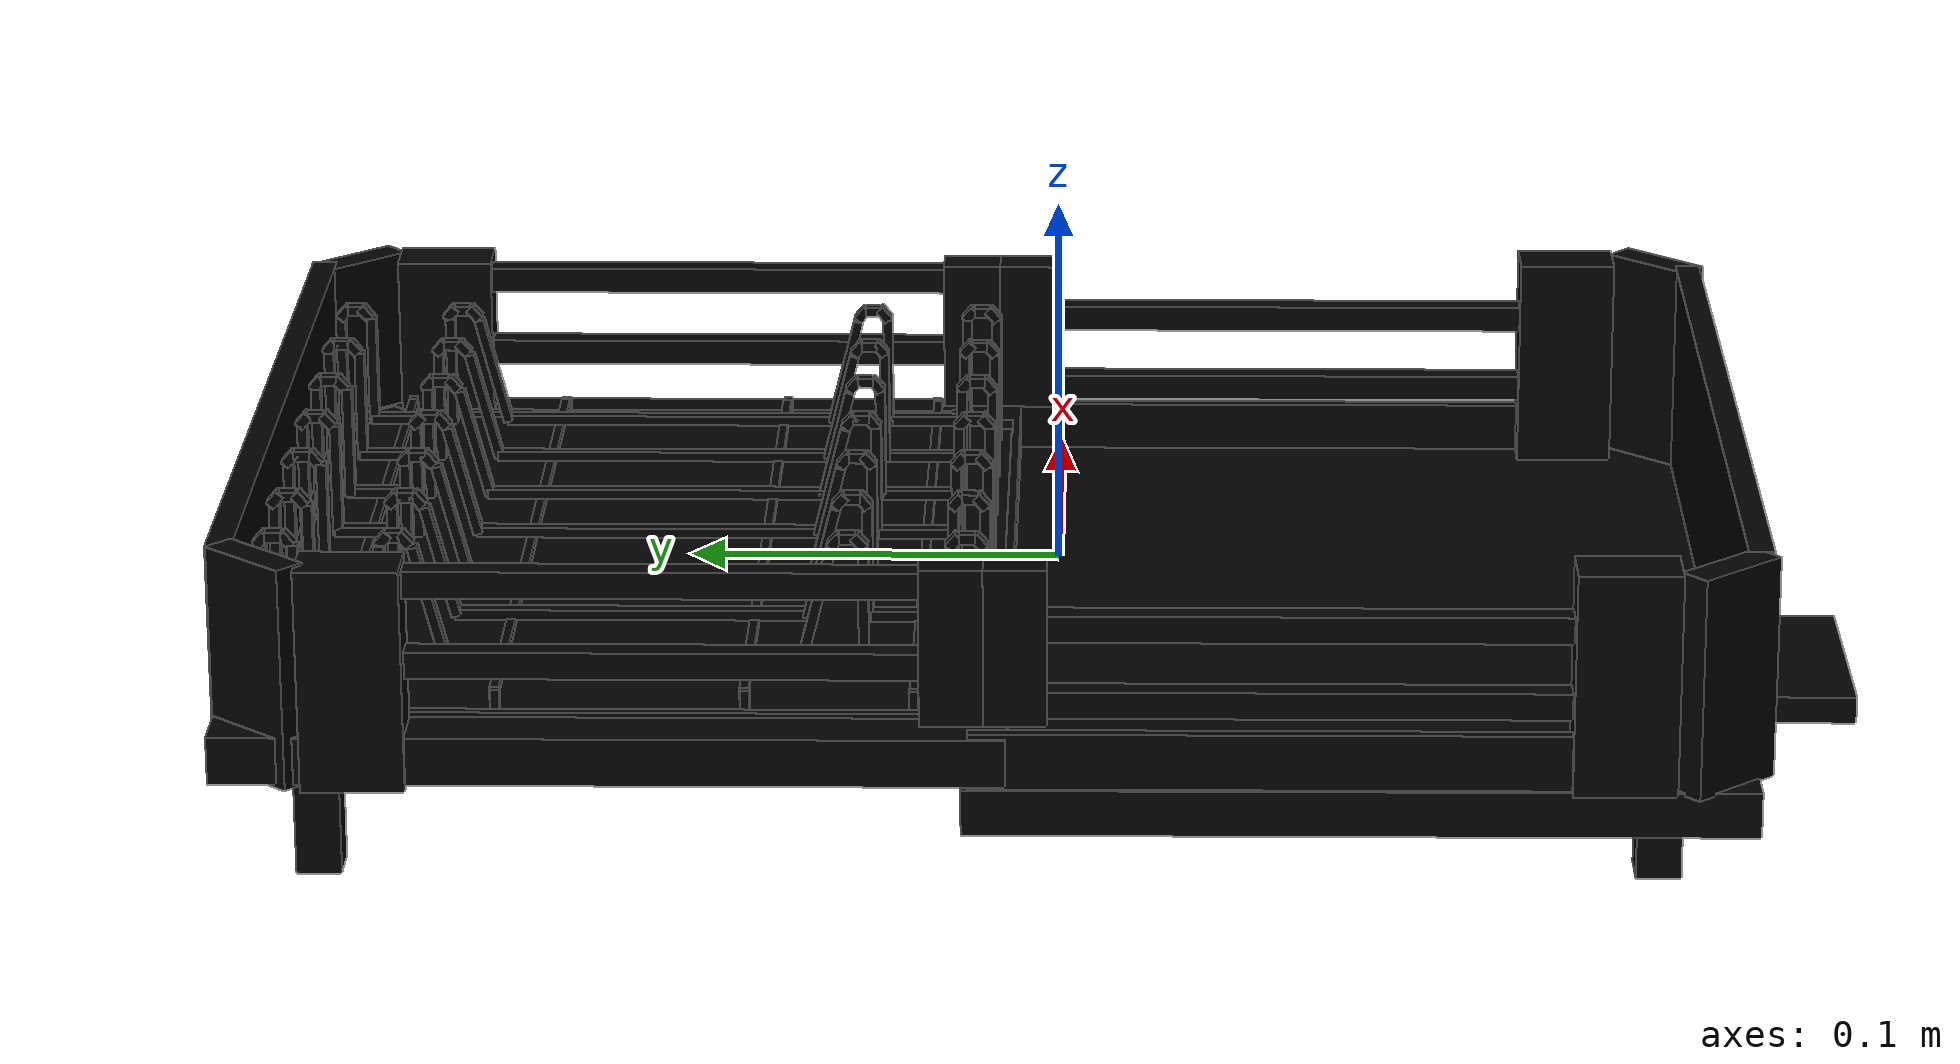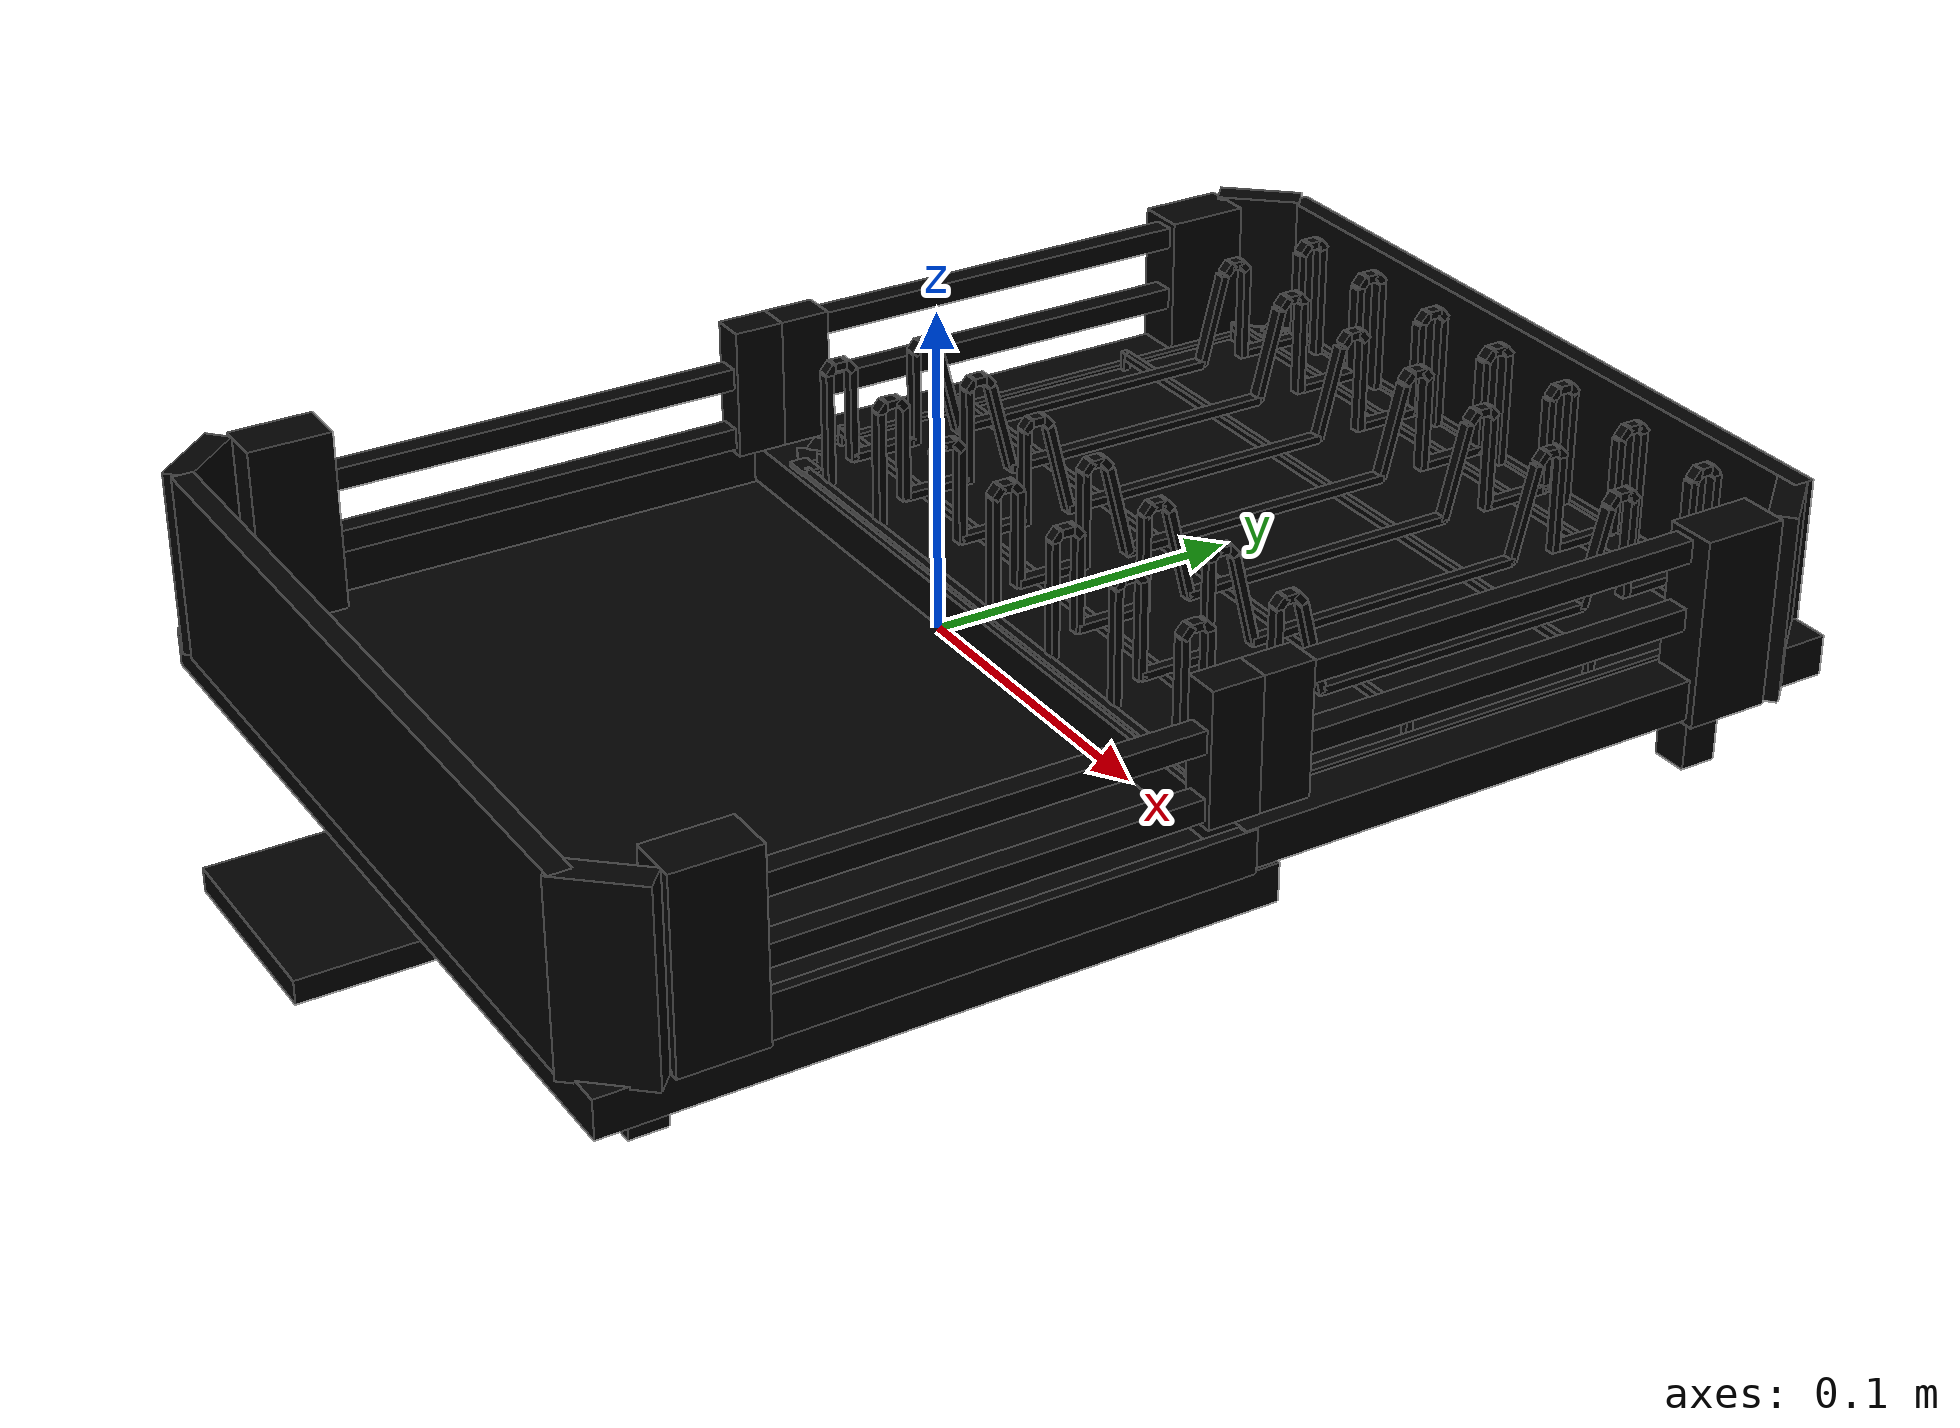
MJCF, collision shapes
<mujoco model="model">
  <option timestep="0.002" gravity="0.0 0.0 -9.81" />
  <compiler angle="radian" />
  <asset>
    <mesh file="visual/DishRack043.obj" name="DishRack043_vis" scale="0.8 0.8 0.8" />
    <texture file="visual/T_BC001.png" name="DishRack043_material" type="2d" />
    <material name="DishRack043_material" rgba="1 1 1 1.0" texture="DishRack043_material" shininess="0.4472135901451111" specular="0.3103448502657381" />
  </asset>
  <default>
    <default class="visual">
      <geom conaffinity="0" contype="0" group="2" type="mesh" density="0" />
    </default>
    <default class="collision">
      <geom group="3" rgba="1 1 1 0.25" density="0" solref="0.004 1" solimp="0.998 0.998 0.001" friction="0.5" />
    </default>
    <default class="spawn">
      <geom group="0" rgba="1 1 1 0.5" contype="0" conaffinity="0" />
      <site group="0" rgba="1 1 1 0.5" />
    </default>
    <default class="region">
      <geom group="1" conaffinity="0" contype="0" rgba="0 1 0 0" mass="0" />
    </default>
  </default>
  <worldbody>
    <body>
      <body name="object">
        <geom mesh="DishRack043_vis" type="mesh" class="visual" material="DishRack043_material" group="2" contype="0" conaffinity="0" density="0" mass="0.5" />
        <geom type="box" pos="0.031169728 0.205674056 0.017716304" size="0.00175487063825 0.00131378648803 0.0197576954961" quat="1.0 0.0 0.0 0.0" class="collision" group="3" rgba="0 0 0 0" density="0" friction="0.5" solref="0.004 1" solimp="0.998 0.998 0.001" />
        <geom type="box" pos="0.031169728 0.202083112 0.039842328" size="0.00175487063825 0.00208327099681 0.00131378676742" quat="1.0 0.0 0.0 0.0" class="collision" group="3" rgba="0 0 0 0" density="0" friction="0.5" solref="0.004 1" solimp="0.998 0.998 0.001" />
        <geom type="box" pos="0.031169728 0.205198696 0.03883036" size="0.00175487063825 0.00131378648803 0.00208327081054" quat="0.9381337761878967 0.3462730050086975 0.0 0.0" class="collision" group="3" rgba="0 0 0 0" density="0" friction="0.5" solref="0.004 1" solimp="0.998 0.998 0.001" />
        <geom type="box" pos="0.031169728 0.198713208 0.03883036" size="0.00175487063825 0.00131378648803 0.00208327081054" quat="0.9381337761878967 -0.3462729752063751 -0.0 0.0" class="collision" group="3" rgba="0 0 0 0" density="0" friction="0.5" solref="0.004 1" solimp="0.998 0.998 0.001" />
        <geom type="box" pos="0.031169728 0.197106936 0.021901056" size="0.00175487063825 0.00131378648803 0.0155729487539" quat="1.0 0.0 0.0 0.0" class="collision" group="3" rgba="0 0 0 0" density="0" friction="0.5" solref="0.004 1" solimp="0.998 0.998 0.001" />
        <geom type="box" pos="0.031169728 0.18682908 0.00721552" size="0.00175487063825 0.0109961859882 0.00131378779188" quat="1.0 0.0 0.0 0.0" class="collision" group="3" rgba="0 0 0 0" density="0" friction="0.5" solref="0.004 1" solimp="0.998 0.998 0.001" />
        <geom type="box" pos="0.031169728 0.17424564 0.03883036" size="0.00175487063825 0.00131378648803 0.00208327081054" quat="0.9381337761878967 0.3462730050086975 0.0 0.0" class="collision" group="3" rgba="0 0 0 0" density="0" friction="0.5" solref="0.004 1" solimp="0.998 0.998 0.001" />
        <geom type="box" pos="0.031169728 0.171130064 0.039842328" size="0.00175487063825 0.00208327099681 0.00131378676742" quat="1.0 0.0 0.0 0.0" class="collision" group="3" rgba="0 0 0 0" density="0" friction="0.5" solref="0.004 1" solimp="0.998 0.998 0.001" />
        <geom type="box" pos="0.031169728 0.174782488 0.021724864" size="0.00175487063825 0.00131378648803 0.0157491385937" quat="1.0 0.0 0.0 0.0" class="collision" group="3" rgba="0 0 0 0" density="0" friction="0.5" solref="0.004 1" solimp="0.998 0.998 0.001" />
        <geom type="box" pos="0.031169728 0.16754892 0.03883036" size="0.00175487063825 0.00131378648803 0.00208327081054" quat="0.9381337761878967 -0.3462729752063751 -0.0 0.0" class="collision" group="3" rgba="0 0 0 0" density="0" friction="0.5" solref="0.004 1" solimp="0.998 0.998 0.001" />
        <geom type="box" pos="0.129307072 0.1011498 0.017551096" size="0.00343731679022 0.0686911225319 0.00354711599648" quat="1.0 0.0 0.0 0.0" class="collision" group="3" rgba="0 0 0 0" density="0" friction="0.5" solref="0.004 1" solimp="0.998 0.998 0.001" />
        <geom type="box" pos="0.031169728 0.162053848 0.021771864" size="0.00175487063825 0.00131378648803 0.0155729487539" quat="0.9922520518302917 -0.12424127757549286 -0.0 0.0" class="collision" group="3" rgba="0 0 0 0" density="0" friction="0.5" solref="0.004 1" solimp="0.998 0.998 0.001" />
        <geom type="box" pos="0.031169728 0.111985984 0.00721552" size="0.00175487063825 0.0469583272934 0.00131379216909" quat="1.0 0.0 0.0 0.0" class="collision" group="3" rgba="0 0 0 0" density="0" friction="0.5" solref="0.004 1" solimp="0.998 0.998 0.001" />
        <geom type="box" pos="0.031169728 0.061872312 0.021771864" size="0.00175487063825 0.00131378648803 0.0155729487539" quat="0.9922520518302917 0.12424127757549286 0.0 0.0" class="collision" group="3" rgba="0 0 0 0" density="0" friction="0.5" solref="0.004 1" solimp="0.998 0.998 0.001" />
        <geom type="box" pos="0.031169728 0.056810848 0.03883036" size="0.00175487063825 0.00131378648803 0.00208327081054" quat="0.9381337761878967 0.3462730050086975 0.0 0.0" class="collision" group="3" rgba="0 0 0 0" density="0" friction="0.5" solref="0.004 1" solimp="0.998 0.998 0.001" />
        <geom type="box" pos="0.031169728 0.049736752 0.021724864" size="0.00175487063825 0.00131378648803 0.0157491385937" quat="1.0 0.0 0.0 0.0" class="collision" group="3" rgba="0 0 0 0" density="0" friction="0.5" solref="0.004 1" solimp="0.998 0.998 0.001" />
        <geom type="box" pos="0.031169728 0.053806832 0.039842328" size="0.00175487063825 0.00208327099681 0.00131378676742" quat="1.0 0.0 0.0 0.0" class="collision" group="3" rgba="0 0 0 0" density="0" friction="0.5" solref="0.004 1" solimp="0.998 0.998 0.001" />
        <geom type="box" pos="0.031169728 0.050691232 0.03883036" size="0.00175487063825 0.00131378648803 0.00208327081054" quat="0.9381337761878967 -0.3462730348110199 -0.0 0.0" class="collision" group="3" rgba="0 0 0 0" density="0" friction="0.5" solref="0.004 1" solimp="0.998 0.998 0.001" />
        <geom type="box" pos="0.031169728 0.038107816 0.00721552" size="0.00175487063825 0.0109961859882 0.00131378779188" quat="1.0 0.0 0.0 0.0" class="collision" group="3" rgba="0 0 0 0" density="0" friction="0.5" solref="0.004 1" solimp="0.998 0.998 0.001" />
        <geom type="box" pos="0.031169728 0.027178152 0.021901056" size="0.00175487063825 0.00131378648803 0.0155729487539" quat="1.0 0.0 0.0 0.0" class="collision" group="3" rgba="0 0 0 0" density="0" friction="0.5" solref="0.004 1" solimp="0.998 0.998 0.001" />
        <geom type="box" pos="0.031169728 0.026223664 0.03883036" size="0.00175487063825 0.00131378648803 0.00208327081054" quat="0.9381337761878967 0.3462730050086975 0.0 0.0" class="collision" group="3" rgba="0 0 0 0" density="0" friction="0.5" solref="0.004 1" solimp="0.998 0.998 0.001" />
        <geom type="box" pos="0.129138864 0.010077304 0.023304488" size="0.00554023385048 0.00818573012948 0.0211288020015" quat="1.0 0.0 0.0 0.0" class="collision" group="3" rgba="0 0 0 0" density="0" friction="0.5" solref="0.004 1" solimp="0.998 0.998 0.001" />
        <geom type="box" pos="0.031169728 0.019738184 0.03883036" size="0.00175487063825 0.00131378648803 0.00208327081054" quat="0.9381337761878967 -0.3462730348110199 -0.0 0.0" class="collision" group="3" rgba="0 0 0 0" density="0" friction="0.5" solref="0.004 1" solimp="0.998 0.998 0.001" />
        <geom type="box" pos="0.031169728 0.022853776 0.039842328" size="0.00175487063825 0.00208327099681 0.00131378676742" quat="1.0 0.0 0.0 0.0" class="collision" group="3" rgba="0 0 0 0" density="0" friction="0.5" solref="0.004 1" solimp="0.998 0.998 0.001" />
        <geom type="box" pos="0.031169728 0.018783696 0.017716304" size="0.00175487063825 0.00131378648803 0.0197576954961" quat="1.0 0.0 0.0 0.0" class="collision" group="3" rgba="0 0 0 0" density="0" friction="0.5" solref="0.004 1" solimp="0.998 0.998 0.001" />
        <geom type="box" pos="0.063655784 0.018783696 0.017716304" size="0.00159593336284 0.00131378648803 0.0197576954961" quat="1.0 0.0 0.0 0.0" class="collision" group="3" rgba="0 0 0 0" density="0" friction="0.5" solref="0.004 1" solimp="0.998 0.998 0.001" />
        <geom type="box" pos="0.063655784 0.022853776 0.039842328" size="0.00159593336284 0.00208327099681 0.00131378676742" quat="1.0 0.0 0.0 0.0" class="collision" group="3" rgba="0 0 0 0" density="0" friction="0.5" solref="0.004 1" solimp="0.998 0.998 0.001" />
        <geom type="box" pos="0.063655784 0.019738184 0.03883036" size="0.00159593336284 0.00131378648803 0.00208327081054" quat="0.9381337761878967 -0.3462730348110199 -0.0 0.0" class="collision" group="3" rgba="0 0 0 0" density="0" friction="0.5" solref="0.004 1" solimp="0.998 0.998 0.001" />
        <geom type="box" pos="0.063655784 0.026223664 0.03883036" size="0.00159593336284 0.00131378648803 0.00208327081054" quat="0.9381337761878967 0.3462730050086975 0.0 0.0" class="collision" group="3" rgba="0 0 0 0" density="0" friction="0.5" solref="0.004 1" solimp="0.998 0.998 0.001" />
        <geom type="box" pos="0.063655784 0.027178152 0.021901056" size="0.00159593336284 0.00131378648803 0.0155729487539" quat="1.0 0.0 0.0 0.0" class="collision" group="3" rgba="0 0 0 0" density="0" friction="0.5" solref="0.004 1" solimp="0.998 0.998 0.001" />
        <geom type="box" pos="0.063655784 0.038107816 0.00721552" size="0.00159593336284 0.0109961859882 0.00131378779188" quat="1.0 0.0 0.0 0.0" class="collision" group="3" rgba="0 0 0 0" density="0" friction="0.5" solref="0.004 1" solimp="0.998 0.998 0.001" />
        <geom type="box" pos="0.063655784 0.050691232 0.03883036" size="0.00159593336284 0.00131378648803 0.00208327081054" quat="0.9381337761878967 -0.3462730348110199 -0.0 0.0" class="collision" group="3" rgba="0 0 0 0" density="0" friction="0.5" solref="0.004 1" solimp="0.998 0.998 0.001" />
        <geom type="box" pos="0.129307072 0.1011498 0.039316536" size="0.00343728922308 0.0686906754971 0.0035470880568" quat="1.0 0.0 0.0 0.0" class="collision" group="3" rgba="0 0 0 0" density="0" friction="0.5" solref="0.004 1" solimp="0.998 0.998 0.001" />
        <geom type="box" pos="0.063655784 0.053806832 0.039842328" size="0.00159593336284 0.00208327099681 0.00131378676742" quat="1.0 0.0 0.0 0.0" class="collision" group="3" rgba="0 0 0 0" density="0" friction="0.5" solref="0.004 1" solimp="0.998 0.998 0.001" />
        <geom type="box" pos="0.063655784 0.049736752 0.021724864" size="0.00159593336284 0.00131378648803 0.0157491385937" quat="1.0 0.0 0.0 0.0" class="collision" group="3" rgba="0 0 0 0" density="0" friction="0.5" solref="0.004 1" solimp="0.998 0.998 0.001" />
        <geom type="box" pos="0.063655784 0.056810848 0.03883036" size="0.00159593336284 0.00131378648803 0.00208327081054" quat="0.9381337761878967 0.3462730050086975 0.0 0.0" class="collision" group="3" rgba="0 0 0 0" density="0" friction="0.5" solref="0.004 1" solimp="0.998 0.998 0.001" />
        <geom type="box" pos="0.063655784 0.061872312 0.021771864" size="0.00159593336284 0.00131378648803 0.0155729487539" quat="0.9922520518302917 0.12424127757549286 0.0 0.0" class="collision" group="3" rgba="0 0 0 0" density="0" friction="0.5" solref="0.004 1" solimp="0.998 0.998 0.001" />
        <geom type="box" pos="0.063655784 0.111985984 0.00721552" size="0.00159593336284 0.0469583272934 0.00131379216909" quat="1.0 0.0 0.0 0.0" class="collision" group="3" rgba="0 0 0 0" density="0" friction="0.5" solref="0.004 1" solimp="0.998 0.998 0.001" />
        <geom type="box" pos="0.063655784 0.162315072 0.021771864" size="0.00159593336284 0.00131378648803 0.0155729487539" quat="0.9922520518302917 -0.12424127757549286 -0.0 0.0" class="collision" group="3" rgba="0 0 0 0" density="0" friction="0.5" solref="0.004 1" solimp="0.998 0.998 0.001" />
        <geom type="box" pos="0.063655784 0.167762208 0.03883036" size="0.00159593336284 0.00131378648803 0.00208327081054" quat="0.9381337761878967 -0.3462729752063751 -0.0 0.0" class="collision" group="3" rgba="0 0 0 0" density="0" friction="0.5" solref="0.004 1" solimp="0.998 0.998 0.001" />
        <geom type="box" pos="0.063655784 0.17487972 0.021724864" size="0.00159593336284 0.00131378648803 0.0157491385937" quat="1.0 0.0 0.0 0.0" class="collision" group="3" rgba="0 0 0 0" density="0" friction="0.5" solref="0.004 1" solimp="0.998 0.998 0.001" />
        <geom type="box" pos="0.063655784 0.171130064 0.039842328" size="0.00159593336284 0.00208327099681 0.00131378676742" quat="1.0 0.0 0.0 0.0" class="collision" group="3" rgba="0 0 0 0" density="0" friction="0.5" solref="0.004 1" solimp="0.998 0.998 0.001" />
        <geom type="box" pos="0.063655784 0.17424564 0.03883036" size="0.00159593336284 0.00131378648803 0.00208327081054" quat="0.9381337761878967 0.3462730050086975 0.0 0.0" class="collision" group="3" rgba="0 0 0 0" density="0" friction="0.5" solref="0.004 1" solimp="0.998 0.998 0.001" />
        <geom type="box" pos="0.129307072 -0.066154584 0.007342728" size="0.00343727618456 0.0686904728412 0.00354707539082" quat="1.0 0.0 0.0 0.0" class="collision" group="3" rgba="0 0 0 0" density="0" friction="0.5" solref="0.004 1" solimp="0.998 0.998 0.001" />
        <geom type="box" pos="0.063655784 0.18682908 0.00721552" size="0.00159593336284 0.0109961859882 0.00131378779188" quat="1.0 0.0 0.0 0.0" class="collision" group="3" rgba="0 0 0 0" density="0" friction="0.5" solref="0.004 1" solimp="0.998 0.998 0.001" />
        <geom type="box" pos="0.063655784 0.1971154 0.021901056" size="0.00159593336284 0.00131378648803 0.0155729487539" quat="1.0 0.0 0.0 0.0" class="collision" group="3" rgba="0 0 0 0" density="0" friction="0.5" solref="0.004 1" solimp="0.998 0.998 0.001" />
        <geom type="box" pos="0.063655784 0.198713208 0.03883036" size="0.00159593336284 0.00131378648803 0.00208327081054" quat="0.9381337761878967 -0.3462729752063751 -0.0 0.0" class="collision" group="3" rgba="0 0 0 0" density="0" friction="0.5" solref="0.004 1" solimp="0.998 0.998 0.001" />
        <geom type="box" pos="0.063655784 0.205198696 0.03883036" size="0.00159593336284 0.00131378648803 0.00208327081054" quat="0.9381337761878967 0.3462730050086975 0.0 0.0" class="collision" group="3" rgba="0 0 0 0" density="0" friction="0.5" solref="0.004 1" solimp="0.998 0.998 0.001" />
        <geom type="box" pos="0.063655784 0.202083112 0.039842328" size="0.00159593336284 0.00208327099681 0.00131378676742" quat="1.0 0.0 0.0 0.0" class="collision" group="3" rgba="0 0 0 0" density="0" friction="0.5" solref="0.004 1" solimp="0.998 0.998 0.001" />
        <geom type="box" pos="0.063655784 0.205661296 0.017716304" size="0.00159593336284 0.00131378648803 0.0197576954961" quat="1.0 0.0 0.0 0.0" class="collision" group="3" rgba="0 0 0 0" density="0" friction="0.5" solref="0.004 1" solimp="0.998 0.998 0.001" />
        <geom type="box" pos="0.095979992 0.205825856 0.017716304" size="0.00180784892291 0.00131378648803 0.0197576954961" quat="1.0 0.0 0.0 0.0" class="collision" group="3" rgba="0 0 0 0" density="0" friction="0.5" solref="0.004 1" solimp="0.998 0.998 0.001" />
        <geom type="box" pos="0.095979992 0.201602336 0.039842328" size="0.00180784892291 0.00208327099681 0.00131378676742" quat="1.0 0.0 0.0 0.0" class="collision" group="3" rgba="0 0 0 0" density="0" friction="0.5" solref="0.004 1" solimp="0.998 0.998 0.001" />
        <geom type="box" pos="0.095979992 0.2045804 0.03883036" size="0.00180784892291 0.00131378648803 0.00208327081054" quat="0.9381337761878967 0.3462730050086975 0.0 0.0" class="collision" group="3" rgba="0 0 0 0" density="0" friction="0.5" solref="0.004 1" solimp="0.998 0.998 0.001" />
        <geom type="box" pos="0.095979992 0.198713208 0.03883036" size="0.00180784892291 0.00131378648803 0.00208327081054" quat="0.9381337761878967 -0.3462729752063751 -0.0 0.0" class="collision" group="3" rgba="0 0 0 0" density="0" friction="0.5" solref="0.004 1" solimp="0.998 0.998 0.001" />
        <geom type="box" pos="0.129138864 0.026306432 0.023304488" size="0.0055401481688 0.0081856444478 0.0211284592748" quat="1.0 0.0 0.0 0.0" class="collision" group="3" rgba="0 0 0 0" density="0" friction="0.5" solref="0.004 1" solimp="0.998 0.998 0.001" />
        <geom type="box" pos="0.095979992 0.197111096 0.021901056" size="0.00180784892291 0.00131378648803 0.0155729487539" quat="1.0 0.0 0.0 0.0" class="collision" group="3" rgba="0 0 0 0" density="0" friction="0.5" solref="0.004 1" solimp="0.998 0.998 0.001" />
        <geom type="box" pos="0.095979992 0.18682908 0.00721552" size="0.00180784892291 0.0109961859882 0.00131378779188" quat="1.0 0.0 0.0 0.0" class="collision" group="3" rgba="0 0 0 0" density="0" friction="0.5" solref="0.004 1" solimp="0.998 0.998 0.001" />
        <geom type="box" pos="0.095979992 0.17424564 0.03883036" size="0.00180784892291 0.00131378648803 0.00208327081054" quat="0.9381337761878967 0.3462730050086975 0.0 0.0" class="collision" group="3" rgba="0 0 0 0" density="0" friction="0.5" solref="0.004 1" solimp="0.998 0.998 0.001" />
        <geom type="box" pos="0.095979992 0.171130064 0.039842328" size="0.00180784892291 0.00208327099681 0.00131378676742" quat="1.0 0.0 0.0 0.0" class="collision" group="3" rgba="0 0 0 0" density="0" friction="0.5" solref="0.004 1" solimp="0.998 0.998 0.001" />
        <geom type="box" pos="0.095979992 0.174617768 0.021724864" size="0.00180784892291 0.00131378648803 0.0157491385937" quat="1.0 0.0 0.0 0.0" class="collision" group="3" rgba="0 0 0 0" density="0" friction="0.5" solref="0.004 1" solimp="0.998 0.998 0.001" />
        <geom type="box" pos="0.095979992 0.167582296 0.03883036" size="0.00180784892291 0.00131378648803 0.00208327081054" quat="0.9381337761878967 -0.3462729752063751 -0.0 0.0" class="collision" group="3" rgba="0 0 0 0" density="0" friction="0.5" solref="0.004 1" solimp="0.998 0.998 0.001" />
        <geom type="box" pos="0.095979992 0.16252084 0.021771864" size="0.00180784892291 0.00131378648803 0.0155729487539" quat="0.9922520518302917 -0.12424127757549286 -0.0 0.0" class="collision" group="3" rgba="0 0 0 0" density="0" friction="0.5" solref="0.004 1" solimp="0.998 0.998 0.001" />
        <geom type="box" pos="0.095979992 0.111985984 0.00721552" size="0.00180784892291 0.0469583272934 0.00131379216909" quat="1.0 0.0 0.0 0.0" class="collision" group="3" rgba="0 0 0 0" density="0" friction="0.5" solref="0.004 1" solimp="0.998 0.998 0.001" />
        <geom type="box" pos="0.095979992 0.061872312 0.021771864" size="0.00180784892291 0.00131378648803 0.0155729487539" quat="0.9922520518302917 0.12424127757549286 0.0 0.0" class="collision" group="3" rgba="0 0 0 0" density="0" friction="0.5" solref="0.004 1" solimp="0.998 0.998 0.001" />
        <geom type="box" pos="0.095979992 0.056810848 0.03883036" size="0.00180784892291 0.00131378648803 0.00208327081054" quat="0.9381337761878967 0.3462730050086975 0.0 0.0" class="collision" group="3" rgba="0 0 0 0" density="0" friction="0.5" solref="0.004 1" solimp="0.998 0.998 0.001" />
        <geom type="box" pos="0.121137552 0.111834456 -0.000459368" size="0.00142243485898 0.0788169622421 0.00158202480524" quat="1.0 0.0 0.0 0.0" class="collision" group="3" rgba="0 0 0 0" density="0" friction="0.5" solref="0.004 1" solimp="0.998 0.998 0.001" />
        <geom type="box" pos="0.095979992 0.049736752 0.021724864" size="0.00180784892291 0.00131378648803 0.0157491385937" quat="1.0 0.0 0.0 0.0" class="collision" group="3" rgba="0 0 0 0" density="0" friction="0.5" solref="0.004 1" solimp="0.998 0.998 0.001" />
        <geom type="box" pos="0.095979992 0.053806832 0.039842328" size="0.00180784892291 0.00208327099681 0.00131378676742" quat="1.0 0.0 0.0 0.0" class="collision" group="3" rgba="0 0 0 0" density="0" friction="0.5" solref="0.004 1" solimp="0.998 0.998 0.001" />
        <geom type="box" pos="0.095979992 0.050691232 0.03883036" size="0.00180784892291 0.00131378648803 0.00208327081054" quat="0.9381337761878967 -0.3462730348110199 -0.0 0.0" class="collision" group="3" rgba="0 0 0 0" density="0" friction="0.5" solref="0.004 1" solimp="0.998 0.998 0.001" />
        <geom type="box" pos="0.095979992 0.038107816 0.00721552" size="0.00180784892291 0.0109961859882 0.00131378779188" quat="1.0 0.0 0.0 0.0" class="collision" group="3" rgba="0 0 0 0" density="0" friction="0.5" solref="0.004 1" solimp="0.998 0.998 0.001" />
        <geom type="box" pos="0.095979992 0.027178152 0.021901056" size="0.00180784892291 0.00131378648803 0.0155729487539" quat="1.0 0.0 0.0 0.0" class="collision" group="3" rgba="0 0 0 0" density="0" friction="0.5" solref="0.004 1" solimp="0.998 0.998 0.001" />
        <geom type="box" pos="0.095979992 0.026223664 0.03883036" size="0.00180784892291 0.00131378648803 0.00208327081054" quat="0.9381337761878967 0.3462730050086975 0.0 0.0" class="collision" group="3" rgba="0 0 0 0" density="0" friction="0.5" solref="0.004 1" solimp="0.998 0.998 0.001" />
        <geom type="box" pos="0.095979992 0.019738184 0.03883036" size="0.00180784892291 0.00131378648803 0.00208327081054" quat="0.9381337761878967 -0.3462730348110199 -0.0 0.0" class="collision" group="3" rgba="0 0 0 0" density="0" friction="0.5" solref="0.004 1" solimp="0.998 0.998 0.001" />
        <geom type="box" pos="0.095979992 0.022853776 0.039842328" size="0.00180784892291 0.00208327099681 0.00131378676742" quat="1.0 0.0 0.0 0.0" class="collision" group="3" rgba="0 0 0 0" density="0" friction="0.5" solref="0.004 1" solimp="0.998 0.998 0.001" />
        <geom type="box" pos="-0.001808912 0.016273344 -0.000459368" size="0.107642388344 0.00151247680188 0.00158202480524" quat="1.0 0.0 0.0 0.0" class="collision" group="3" rgba="0 0 0 0" density="0" friction="0.5" solref="0.004 1" solimp="0.998 0.998 0.001" />
        <geom type="box" pos="0.095979992 0.018783696 0.017716304" size="0.00180784892291 0.00131378648803 0.0197576954961" quat="1.0 0.0 0.0 0.0" class="collision" group="3" rgba="0 0 0 0" density="0" friction="0.5" solref="0.004 1" solimp="0.998 0.998 0.001" />
        <geom type="box" pos="0.001556016 -0.179855552 0.015250488" size="0.123519229889 0.00339460074901 0.0297877907753" quat="1.0 0.0 0.0 0.0" class="collision" group="3" rgba="0 0 0 0" density="0" friction="0.5" solref="0.004 1" solimp="0.998 0.998 0.001" />
        <geom type="box" pos="0.120060272 0.028745744 -0.000459368" size="0.00447872132063 0.00304220579564 0.00158202480524" quat="0.9153963327407837 0.0 0.0 0.40255382657051086" class="collision" group="3" rgba="0 0 0 0" density="0" friction="0.5" solref="0.004 1" solimp="0.998 0.998 0.001" />
        <geom type="box" pos="0.115841976 0.021728792 -0.000459368" size="0.00447872132063 0.00304220598191 0.00158202480524" quat="0.9722712635993958 0.0 0.0 0.23385590314865112" class="collision" group="3" rgba="0 0 0 0" density="0" friction="0.5" solref="0.004 1" solimp="0.998 0.998 0.001" />
        <geom type="box" pos="0.109514552 0.017429376 -0.000459368" size="0.00447872132063 0.00304220579564 0.00158202480524" quat="1.0 0.0 0.0 0.0" class="collision" group="3" rgba="0 0 0 0" density="0" friction="0.5" solref="0.004 1" solimp="0.998 0.998 0.001" />
        <geom type="box" pos="-0.001595104 0.114214488 -0.006542016" size="0.13858397007 0.101753473282 0.00638917386532" quat="1.0 0.0 0.0 0.0" class="collision" group="3" rgba="0 0 0 0" density="0" friction="0.5" solref="0.004 1" solimp="0.998 0.998 0.001" />
        <geom type="box" pos="-0.137399672 -0.056320592 -0.006685176" size="0.00171609632671 0.0784195244312 0.00785090699792" quat="1.0 0.0 0.0 0.0" class="collision" group="3" rgba="0 0 0 0" density="0" friction="0.5" solref="0.004 1" solimp="0.998 0.998 0.001" />
        <geom type="box" pos="0.135540968 -0.059338224 -0.007511064" size="0.00171609539539 0.0754018247127 0.00702501237392" quat="1.0 0.0 0.0 0.0" class="collision" group="3" rgba="0 0 0 0" density="0" friction="0.5" solref="0.004 1" solimp="0.998 0.998 0.001" />
        <geom type="box" pos="-0.001595104 -0.078340352 -0.01990592" size="0.138583755493 0.10222414732 0.0061403285712" quat="1.0 0.0 0.0 0.0" class="collision" group="3" rgba="0 0 0 0" density="0" friction="0.5" solref="0.004 1" solimp="0.998 0.998 0.001" />
        <geom type="box" pos="0.129307072 -0.06553656 0.028290344" size="0.00343721844256 0.0686895430088 0.00354701764882" quat="1.0 0.0 0.0 0.0" class="collision" group="3" rgba="0 0 0 0" density="0" friction="0.5" solref="0.004 1" solimp="0.998 0.998 0.001" />
        <geom type="box" pos="-0.000948384 -0.158495888 -0.03179764" size="0.0320948511362 0.0572251081467 0.00373337455094" quat="1.0 0.0 0.0 0.0" class="collision" group="3" rgba="0 0 0 0" density="0" friction="0.5" solref="0.004 1" solimp="0.998 0.998 0.001" />
        <geom type="box" pos="-0.0661658 0.004678904 -0.032827944" size="0.00597956180572 0.00593638084828 0.0129646763205" quat="1.0 0.0 0.0 0.0" class="collision" group="3" rgba="0 0 0 0" density="0" friction="0.5" solref="0.004 1" solimp="0.998 0.998 0.001" />
        <geom type="box" pos="0.128863792 0.203818536 0.015250488" size="0.00434559099376 0.0136276826262 0.0297861814499" quat="0.9338935613632202 0.0 0.0 0.35755112767219543" class="collision" group="3" rgba="0 0 0 0" density="0" friction="0.5" solref="0.004 1" solimp="0.998 0.998 0.001" />
        <geom type="box" pos="0.062365688 0.004678904 -0.032827944" size="0.00597955733538 0.00593637675047 0.0129646673798" quat="1.0 0.0 0.0 0.0" class="collision" group="3" rgba="0 0 0 0" density="0" friction="0.5" solref="0.004 1" solimp="0.998 0.998 0.001" />
        <geom type="box" pos="0.111136608 -0.156300904 -0.032827944" size="0.00597955323756 0.00593637228012 0.0129646599292" quat="1.0 0.0 0.0 0.0" class="collision" group="3" rgba="0 0 0 0" density="0" friction="0.5" solref="0.004 1" solimp="0.998 0.998 0.001" />
        <geom type="box" pos="-0.113092824 -0.156300904 -0.032827944" size="0.00597954876721 0.0059363681823 0.0129646509886" quat="1.0 0.0 0.0 0.0" class="collision" group="3" rgba="0 0 0 0" density="0" friction="0.5" solref="0.004 1" solimp="0.998 0.998 0.001" />
        <geom type="box" pos="-0.113092824 0.19082316 -0.024889864" size="0.00597954466939 0.00593636371196 0.0209034204483" quat="1.0 0.0 0.0 0.0" class="collision" group="3" rgba="0 0 0 0" density="0" friction="0.5" solref="0.004 1" solimp="0.998 0.998 0.001" />
        <geom type="box" pos="0.111136608 0.19082316 -0.024889864" size="0.00597954019904 0.00593635961413 0.0209034025669" quat="1.0 0.0 0.0 0.0" class="collision" group="3" rgba="0 0 0 0" density="0" friction="0.5" solref="0.004 1" solimp="0.998 0.998 0.001" />
        <geom type="box" pos="-0.120379464 0.188258384 -0.001816184" size="0.00112094851211 0.00115728173405 0.00792363137007" quat="1.0 0.0 0.0 0.0" class="collision" group="3" rgba="0 0 0 0" density="0" friction="0.5" solref="0.004 1" solimp="0.998 0.998 0.001" />
        <geom type="box" pos="-0.001541224 0.188176584 0.004769888" size="0.119256734848 0.00115728173405 0.00121049694717" quat="1.0 0.0 0.0 0.0" class="collision" group="3" rgba="0 0 0 0" density="0" friction="0.5" solref="0.004 1" solimp="0.998 0.998 0.001" />
        <geom type="box" pos="0.118373792 0.188258384 -0.001816184" size="0.00112094851211 0.00115728173405 0.00792363137007" quat="1.0 0.0 0.0 0.0" class="collision" group="3" rgba="0 0 0 0" density="0" friction="0.5" solref="0.004 1" solimp="0.998 0.998 0.001" />
        <geom type="box" pos="0.118373792 0.143786952 -0.001816184" size="0.00112094851211 0.00115728173405 0.00792363137007" quat="1.0 0.0 0.0 0.0" class="collision" group="3" rgba="0 0 0 0" density="0" friction="0.5" solref="0.004 1" solimp="0.998 0.998 0.001" />
        <geom type="box" pos="-0.001541224 0.144090736 0.004769888" size="0.119256734848 0.00115728173405 0.00121049694717" quat="1.0 0.0 0.0 0.0" class="collision" group="3" rgba="0 0 0 0" density="0" friction="0.5" solref="0.004 1" solimp="0.998 0.998 0.001" />
        <geom type="box" pos="0.131538272 0.178824592 0.015250488" size="0.00793942064047 0.0133936792612 0.02978746593" quat="1.0 0.0 0.0 0.0" class="collision" group="3" rgba="0 0 0 0" density="0" friction="0.5" solref="0.004 1" solimp="0.998 0.998 0.001" />
        <geom type="box" pos="-0.120379464 0.143786952 -0.001816184" size="0.00112094851211 0.00115728173405 0.00792363137007" quat="1.0 0.0 0.0 0.0" class="collision" group="3" rgba="0 0 0 0" density="0" friction="0.5" solref="0.004 1" solimp="0.998 0.998 0.001" />
        <geom type="box" pos="-0.120379464 0.07955412 -0.001816184" size="0.00112094851211 0.00115728173405 0.00792363137007" quat="1.0 0.0 0.0 0.0" class="collision" group="3" rgba="0 0 0 0" density="0" friction="0.5" solref="0.004 1" solimp="0.998 0.998 0.001" />
        <geom type="box" pos="-0.001541224 0.079890432 0.004769888" size="0.119256734848 0.00115728173405 0.00121049694717" quat="1.0 0.0 0.0 0.0" class="collision" group="3" rgba="0 0 0 0" density="0" friction="0.5" solref="0.004 1" solimp="0.998 0.998 0.001" />
        <geom type="box" pos="0.118373792 0.07955412 -0.001816184" size="0.00112094851211 0.00115728173405 0.00792363137007" quat="1.0 0.0 0.0 0.0" class="collision" group="3" rgba="0 0 0 0" density="0" friction="0.5" solref="0.004 1" solimp="0.998 0.998 0.001" />
        <geom type="box" pos="0.118373792 0.03623252 -0.001816184" size="0.00112094851211 0.00115728173405 0.00792363137007" quat="1.0 0.0 0.0 0.0" class="collision" group="3" rgba="0 0 0 0" density="0" friction="0.5" solref="0.004 1" solimp="0.998 0.998 0.001" />
        <geom type="box" pos="-0.001541224 0.036150712 0.004769888" size="0.119256734848 0.00115728173405 0.00121049694717" quat="1.0 0.0 0.0 0.0" class="collision" group="3" rgba="0 0 0 0" density="0" friction="0.5" solref="0.004 1" solimp="0.998 0.998 0.001" />
        <geom type="box" pos="-0.120379464 0.03623252 -0.001816184" size="0.00112094851211 0.00115728173405 0.00792363137007" quat="1.0 0.0 0.0 0.0" class="collision" group="3" rgba="0 0 0 0" density="0" friction="0.5" solref="0.004 1" solimp="0.998 0.998 0.001" />
        <geom type="box" pos="0.109514552 0.20711336 -0.000459368" size="0.00447872132063 0.00304220579564 0.00158202480524" quat="1.0 0.0 0.0 0.0" class="collision" group="3" rgba="0 0 0 0" density="0" friction="0.5" solref="0.004 1" solimp="0.998 0.998 0.001" />
        <geom type="box" pos="0.115841976 0.20281396 -0.000459368" size="0.00447872132063 0.00304220579564 0.00158202480524" quat="0.9722712635993958 0.0 -0.0 -0.23385585844516754" class="collision" group="3" rgba="0 0 0 0" density="0" friction="0.5" solref="0.004 1" solimp="0.998 0.998 0.001" />
        <geom type="box" pos="0.120060272 0.195796976 -0.000459368" size="0.00447872132063 0.00304220598191 0.00158202480524" quat="0.9153962731361389 0.0 -0.0 -0.40255388617515564" class="collision" group="3" rgba="0 0 0 0" density="0" friction="0.5" solref="0.004 1" solimp="0.998 0.998 0.001" />
        <geom type="box" pos="0.001556016 0.213304376 0.015250488" size="0.12351731062 0.00339454077184 0.0297873109579" quat="1.0 0.0 0.0 0.0" class="collision" group="3" rgba="0 0 0 0" density="0" friction="0.5" solref="0.004 1" solimp="0.998 0.998 0.001" />
        <geom type="box" pos="0.131538272 -0.145375768 0.015250488" size="0.00793937817216 0.0133935943246 0.0297872930765" quat="1.0 0.0 0.0 0.0" class="collision" group="3" rgba="0 0 0 0" density="0" friction="0.5" solref="0.004 1" solimp="0.998 0.998 0.001" />
        <geom type="box" pos="-0.001808912 0.208269384 -0.000459368" size="0.107642388344 0.00151247680188 0.00158202480524" quat="1.0 0.0 0.0 0.0" class="collision" group="3" rgba="0 0 0 0" density="0" friction="0.5" solref="0.004 1" solimp="0.998 0.998 0.001" />
        <geom type="box" pos="-0.121945568 0.195796976 -0.000459368" size="0.00447872132063 0.00304220598191 0.00158202480524" quat="0.9153962731361389 0.0 0.0 0.40255388617515564" class="collision" group="3" rgba="0 0 0 0" density="0" friction="0.5" solref="0.004 1" solimp="0.998 0.998 0.001" />
        <geom type="box" pos="-0.117727272 0.20281396 -0.000459368" size="0.00447872132063 0.00304220579564 0.00158202480524" quat="0.9722712635993958 0.0 0.0 0.23385585844516754" class="collision" group="3" rgba="0 0 0 0" density="0" friction="0.5" solref="0.004 1" solimp="0.998 0.998 0.001" />
        <geom type="box" pos="-0.11139984 0.20711336 -0.000459368" size="0.00447872132063 0.00304220579564 0.00158202480524" quat="1.0 0.0 0.0 0.0" class="collision" group="3" rgba="0 0 0 0" density="0" friction="0.5" solref="0.004 1" solimp="0.998 0.998 0.001" />
        <geom type="box" pos="-0.123022848 0.111834456 -0.000459368" size="0.00142243485898 0.0788169622421 0.00158202480524" quat="1.0 0.0 0.0 0.0" class="collision" group="3" rgba="0 0 0 0" density="0" friction="0.5" solref="0.004 1" solimp="0.998 0.998 0.001" />
        <geom type="box" pos="-0.11139984 0.017429376 -0.000459368" size="0.00447872132063 0.00304220579564 0.00158202480524" quat="1.0 0.0 0.0 0.0" class="collision" group="3" rgba="0 0 0 0" density="0" friction="0.5" solref="0.004 1" solimp="0.998 0.998 0.001" />
        <geom type="box" pos="-0.117727272 0.021728792 -0.000459368" size="0.00447872132063 0.00304220579564 0.00158202480524" quat="0.9722712635993958 0.0 -0.0 -0.23385585844516754" class="collision" group="3" rgba="0 0 0 0" density="0" friction="0.5" solref="0.004 1" solimp="0.998 0.998 0.001" />
        <geom type="box" pos="-0.121945568 0.028745744 -0.000459368" size="0.00447872132063 0.00304220598191 0.00158202480524" quat="0.9153962731361389 0.0 -0.0 -0.40255388617515564" class="collision" group="3" rgba="0 0 0 0" density="0" friction="0.5" solref="0.004 1" solimp="0.998 0.998 0.001" />
        <geom type="box" pos="-0.033404848 0.20575316 0.017716304" size="0.00180784873664 0.00131378648803 0.0197576954961" quat="1.0 0.0 0.0 0.0" class="collision" group="3" rgba="0 0 0 0" density="0" friction="0.5" solref="0.004 1" solimp="0.998 0.998 0.001" />
        <geom type="box" pos="-0.033404856 0.202083112 0.039842328" size="0.00180784873664 0.00208327099681 0.00131378676742" quat="1.0 0.0 0.0 0.0" class="collision" group="3" rgba="0 0 0 0" density="0" friction="0.5" solref="0.004 1" solimp="0.998 0.998 0.001" />
        <geom type="box" pos="-0.133213984 0.178824568 0.015250488" size="0.00801560878754 0.0133935332299 0.0297871738672" quat="1.0 0.0 0.0 0.0" class="collision" group="3" rgba="0 0 0 0" density="0" friction="0.5" solref="0.004 1" solimp="0.998 0.998 0.001" />
        <geom type="box" pos="-0.033404856 0.205198696 0.03883036" size="0.00180784873664 0.00131378648803 0.00208327081054" quat="0.9381337761878967 0.3462730050086975 0.0 0.0" class="collision" group="3" rgba="0 0 0 0" density="0" friction="0.5" solref="0.004 1" solimp="0.998 0.998 0.001" />
        <geom type="box" pos="-0.033404856 0.198713208 0.03883036" size="0.00180784873664 0.00131378648803 0.00208327081054" quat="0.9381337761878967 -0.3462729752063751 -0.0 0.0" class="collision" group="3" rgba="0 0 0 0" density="0" friction="0.5" solref="0.004 1" solimp="0.998 0.998 0.001" />
        <geom type="box" pos="-0.033404856 0.196941888 0.021901056" size="0.00180784873664 0.00131378648803 0.0155729487539" quat="1.0 0.0 0.0 0.0" class="collision" group="3" rgba="0 0 0 0" density="0" friction="0.5" solref="0.004 1" solimp="0.998 0.998 0.001" />
        <geom type="box" pos="-0.033404856 0.18682908 0.00721552" size="0.00180784873664 0.0109961859882 0.00131378779188" quat="1.0 0.0 0.0 0.0" class="collision" group="3" rgba="0 0 0 0" density="0" friction="0.5" solref="0.004 1" solimp="0.998 0.998 0.001" />
        <geom type="box" pos="-0.033404856 0.17424564 0.03883036" size="0.00180784873664 0.00131378648803 0.00208327081054" quat="0.9381337761878967 0.3462730050086975 0.0 0.0" class="collision" group="3" rgba="0 0 0 0" density="0" friction="0.5" solref="0.004 1" solimp="0.998 0.998 0.001" />
        <geom type="box" pos="-0.033404856 0.171130064 0.039842328" size="0.00180784873664 0.00208327099681 0.00131378676742" quat="1.0 0.0 0.0 0.0" class="collision" group="3" rgba="0 0 0 0" density="0" friction="0.5" solref="0.004 1" solimp="0.998 0.998 0.001" />
        <geom type="box" pos="-0.033404856 0.174560952 0.021724864" size="0.00180784873664 0.00131378648803 0.0157491385937" quat="1.0 0.0 0.0 0.0" class="collision" group="3" rgba="0 0 0 0" density="0" friction="0.5" solref="0.004 1" solimp="0.998 0.998 0.001" />
        <geom type="box" pos="-0.033404856 0.168126032 0.03883036" size="0.00180784873664 0.00131378648803 0.00208327081054" quat="0.9381337761878967 -0.3462729752063751 -0.0 0.0" class="collision" group="3" rgba="0 0 0 0" density="0" friction="0.5" solref="0.004 1" solimp="0.998 0.998 0.001" />
        <geom type="box" pos="-0.033404856 0.162331072 0.021771864" size="0.00180784873664 0.00131378648803 0.0155729487539" quat="0.9922520518302917 -0.12424127757549286 -0.0 0.0" class="collision" group="3" rgba="0 0 0 0" density="0" friction="0.5" solref="0.004 1" solimp="0.998 0.998 0.001" />
        <geom type="box" pos="-0.033404856 0.111985984 0.00721552" size="0.00180784873664 0.0469583272934 0.00131379216909" quat="1.0 0.0 0.0 0.0" class="collision" group="3" rgba="0 0 0 0" density="0" friction="0.5" solref="0.004 1" solimp="0.998 0.998 0.001" />
        <geom type="box" pos="-0.12996828 0.20313928 0.015991616" size="0.00434559099376 0.0136276826262 0.0297861814499" quat="0.9338935613632202 0.0 -0.0 -0.35755112767219543" class="collision" group="3" rgba="0 0 0 0" density="0" friction="0.5" solref="0.004 1" solimp="0.998 0.998 0.001" />
        <geom type="box" pos="-0.033404856 0.061872312 0.021771864" size="0.00180784873664 0.00131378648803 0.0155729487539" quat="0.9922520518302917 0.12424127757549286 0.0 0.0" class="collision" group="3" rgba="0 0 0 0" density="0" friction="0.5" solref="0.004 1" solimp="0.998 0.998 0.001" />
        <geom type="box" pos="-0.033404856 0.056810848 0.03883036" size="0.00180784873664 0.00131378648803 0.00208327081054" quat="0.9381337761878967 0.3462730050086975 0.0 0.0" class="collision" group="3" rgba="0 0 0 0" density="0" friction="0.5" solref="0.004 1" solimp="0.998 0.998 0.001" />
        <geom type="box" pos="-0.033404856 0.049736752 0.021724864" size="0.00180784873664 0.00131378648803 0.0157491385937" quat="1.0 0.0 0.0 0.0" class="collision" group="3" rgba="0 0 0 0" density="0" friction="0.5" solref="0.004 1" solimp="0.998 0.998 0.001" />
        <geom type="box" pos="-0.033404856 0.053806832 0.039842328" size="0.00180784873664 0.00208327099681 0.00131378676742" quat="1.0 0.0 0.0 0.0" class="collision" group="3" rgba="0 0 0 0" density="0" friction="0.5" solref="0.004 1" solimp="0.998 0.998 0.001" />
        <geom type="box" pos="-0.033404856 0.050691232 0.03883036" size="0.00180784873664 0.00131378648803 0.00208327081054" quat="0.9381337761878967 -0.3462730348110199 -0.0 0.0" class="collision" group="3" rgba="0 0 0 0" density="0" friction="0.5" solref="0.004 1" solimp="0.998 0.998 0.001" />
        <geom type="box" pos="-0.033404856 0.038107816 0.00721552" size="0.00180784873664 0.0109961859882 0.00131378779188" quat="1.0 0.0 0.0 0.0" class="collision" group="3" rgba="0 0 0 0" density="0" friction="0.5" solref="0.004 1" solimp="0.998 0.998 0.001" />
        <geom type="box" pos="-0.033404856 0.027178152 0.021901056" size="0.00180784873664 0.00131378648803 0.0155729487539" quat="1.0 0.0 0.0 0.0" class="collision" group="3" rgba="0 0 0 0" density="0" friction="0.5" solref="0.004 1" solimp="0.998 0.998 0.001" />
        <geom type="box" pos="-0.033404856 0.026223664 0.03883036" size="0.00180784873664 0.00131378648803 0.00208327081054" quat="0.9381337761878967 0.3462730050086975 0.0 0.0" class="collision" group="3" rgba="0 0 0 0" density="0" friction="0.5" solref="0.004 1" solimp="0.998 0.998 0.001" />
        <geom type="box" pos="-0.033404856 0.019738184 0.03883036" size="0.00180784873664 0.00131378648803 0.00208327081054" quat="0.9381337761878967 -0.3462730348110199 -0.0 0.0" class="collision" group="3" rgba="0 0 0 0" density="0" friction="0.5" solref="0.004 1" solimp="0.998 0.998 0.001" />
        <geom type="box" pos="-0.033404856 0.022853776 0.039842328" size="0.00180784873664 0.00208327099681 0.00131378676742" quat="1.0 0.0 0.0 0.0" class="collision" group="3" rgba="0 0 0 0" density="0" friction="0.5" solref="0.004 1" solimp="0.998 0.998 0.001" />
        <geom type="box" pos="-0.131776328 -0.171415016 0.015250488" size="0.00434559099376 0.0136276826262 0.0297861814499" quat="0.9338935613632202 0.0 0.0 0.35755112767219543" class="collision" group="3" rgba="0 0 0 0" density="0" friction="0.5" solref="0.004 1" solimp="0.998 0.998 0.001" />
        <geom type="box" pos="-0.033404848 0.018783696 0.017716304" size="0.00180784873664 0.00131378648803 0.0197576954961" quat="1.0 0.0 0.0 0.0" class="collision" group="3" rgba="0 0 0 0" density="0" friction="0.5" solref="0.004 1" solimp="0.998 0.998 0.001" />
        <geom type="box" pos="-0.098303 0.018783696 0.017716304" size="0.00189261548221 0.00131378648803 0.0197576954961" quat="1.0 0.0 0.0 0.0" class="collision" group="3" rgba="0 0 0 0" density="0" friction="0.5" solref="0.004 1" solimp="0.998 0.998 0.001" />
        <geom type="box" pos="-0.098303008 0.022853776 0.039842328" size="0.00189261548221 0.00208327099681 0.00131378676742" quat="1.0 0.0 0.0 0.0" class="collision" group="3" rgba="0 0 0 0" density="0" friction="0.5" solref="0.004 1" solimp="0.998 0.998 0.001" />
        <geom type="box" pos="-0.098303008 0.019738184 0.03883036" size="0.00189261548221 0.00131378648803 0.00208327081054" quat="0.9381337761878967 -0.3462730348110199 -0.0 0.0" class="collision" group="3" rgba="0 0 0 0" density="0" friction="0.5" solref="0.004 1" solimp="0.998 0.998 0.001" />
        <geom type="box" pos="-0.098303008 0.026223664 0.03883036" size="0.00189261548221 0.00131378648803 0.00208327081054" quat="0.9381337761878967 0.3462730050086975 0.0 0.0" class="collision" group="3" rgba="0 0 0 0" density="0" friction="0.5" solref="0.004 1" solimp="0.998 0.998 0.001" />
        <geom type="box" pos="-0.098303008 0.027178152 0.021901056" size="0.00189261548221 0.00131378648803 0.0155729487539" quat="1.0 0.0 0.0 0.0" class="collision" group="3" rgba="0 0 0 0" density="0" friction="0.5" solref="0.004 1" solimp="0.998 0.998 0.001" />
        <geom type="box" pos="-0.098303008 0.038107816 0.00721552" size="0.00189261548221 0.0109961859882 0.00131378779188" quat="1.0 0.0 0.0 0.0" class="collision" group="3" rgba="0 0 0 0" density="0" friction="0.5" solref="0.004 1" solimp="0.998 0.998 0.001" />
        <geom type="box" pos="-0.098303008 0.050691232 0.03883036" size="0.00189261548221 0.00131378648803 0.00208327081054" quat="0.9381337761878967 -0.3462730348110199 -0.0 0.0" class="collision" group="3" rgba="0 0 0 0" density="0" friction="0.5" solref="0.004 1" solimp="0.998 0.998 0.001" />
        <geom type="box" pos="-0.098303008 0.053806832 0.039842328" size="0.00189261548221 0.00208327099681 0.00131378676742" quat="1.0 0.0 0.0 0.0" class="collision" group="3" rgba="0 0 0 0" density="0" friction="0.5" solref="0.004 1" solimp="0.998 0.998 0.001" />
        <geom type="box" pos="-0.098303008 0.049736752 0.021724864" size="0.00189261548221 0.00131378648803 0.0157491385937" quat="1.0 0.0 0.0 0.0" class="collision" group="3" rgba="0 0 0 0" density="0" friction="0.5" solref="0.004 1" solimp="0.998 0.998 0.001" />
        <geom type="box" pos="-0.13329024 -0.145375752 0.015250488" size="0.0079392708838 0.0133933797479 0.0297868639231" quat="1.0 0.0 0.0 0.0" class="collision" group="3" rgba="0 0 0 0" density="0" friction="0.5" solref="0.004 1" solimp="0.998 0.998 0.001" />
        <geom type="box" pos="-0.098303008 0.056810848 0.03883036" size="0.00189261548221 0.00131378648803 0.00208327081054" quat="0.9381337761878967 0.3462730050086975 0.0 0.0" class="collision" group="3" rgba="0 0 0 0" density="0" friction="0.5" solref="0.004 1" solimp="0.998 0.998 0.001" />
        <geom type="box" pos="-0.098303008 0.061872312 0.021771864" size="0.00189261548221 0.00131378648803 0.0155729487539" quat="0.9922520518302917 0.12424127757549286 0.0 0.0" class="collision" group="3" rgba="0 0 0 0" density="0" friction="0.5" solref="0.004 1" solimp="0.998 0.998 0.001" />
        <geom type="box" pos="-0.098128944 0.111985984 0.00721552" size="0.00189261548221 0.0469583272934 0.00131379216909" quat="1.0 0.0 0.0 0.0" class="collision" group="3" rgba="0 0 0 0" density="0" friction="0.5" solref="0.004 1" solimp="0.998 0.998 0.001" />
        <geom type="box" pos="-0.098128944 0.16241552 0.021771864" size="0.00189261548221 0.00131378648803 0.0155729487539" quat="0.9922520518302917 -0.12424127757549286 -0.0 0.0" class="collision" group="3" rgba="0 0 0 0" density="0" friction="0.5" solref="0.004 1" solimp="0.998 0.998 0.001" />
        <geom type="box" pos="-0.09789396 0.168126032 0.03883036" size="0.00189261548221 0.00131378648803 0.00208327081054" quat="0.9381337761878967 -0.3462729752063751 -0.0 0.0" class="collision" group="3" rgba="0 0 0 0" density="0" friction="0.5" solref="0.004 1" solimp="0.998 0.998 0.001" />
        <geom type="box" pos="-0.098128944 0.174853016 0.021724864" size="0.00189261548221 0.00131378648803 0.0157491385937" quat="1.0 0.0 0.0 0.0" class="collision" group="3" rgba="0 0 0 0" density="0" friction="0.5" solref="0.004 1" solimp="0.998 0.998 0.001" />
        <geom type="box" pos="-0.09789396 0.171130064 0.039842328" size="0.00189261548221 0.00208327099681 0.00131378676742" quat="1.0 0.0 0.0 0.0" class="collision" group="3" rgba="0 0 0 0" density="0" friction="0.5" solref="0.004 1" solimp="0.998 0.998 0.001" />
        <geom type="box" pos="-0.09789396 0.17363256 0.03883036" size="0.00189261548221 0.00131378648803 0.00208327081054" quat="0.9381337761878967 0.3462730050086975 0.0 0.0" class="collision" group="3" rgba="0 0 0 0" density="0" friction="0.5" solref="0.004 1" solimp="0.998 0.998 0.001" />
        <geom type="box" pos="-0.098128944 0.18682908 0.00721552" size="0.00189261548221 0.0109961859882 0.00131378779188" quat="1.0 0.0 0.0 0.0" class="collision" group="3" rgba="0 0 0 0" density="0" friction="0.5" solref="0.004 1" solimp="0.998 0.998 0.001" />
        <geom type="box" pos="-0.09816668 0.197115376 0.021901056" size="0.00189261548221 0.00131378648803 0.0155729487539" quat="1.0 0.0 0.0 0.0" class="collision" group="3" rgba="0 0 0 0" density="0" friction="0.5" solref="0.004 1" solimp="0.998 0.998 0.001" />
        <geom type="box" pos="-0.131059032 -0.066154584 0.02793192" size="0.00343710258603 0.0686876952648 0.00354690179228" quat="1.0 0.0 0.0 0.0" class="collision" group="3" rgba="0 0 0 0" density="0" friction="0.5" solref="0.004 1" solimp="0.998 0.998 0.001" />
        <geom type="box" pos="-0.098128944 0.198713208 0.03883036" size="0.00189261548221 0.00131378648803 0.00208327081054" quat="0.9381337761878967 -0.3462729752063751 -0.0 0.0" class="collision" group="3" rgba="0 0 0 0" density="0" friction="0.5" solref="0.004 1" solimp="0.998 0.998 0.001" />
        <geom type="box" pos="-0.098224232 0.205198696 0.03883036" size="0.00189261548221 0.00131378648803 0.00208327081054" quat="0.9381337761878967 0.3462730050086975 0.0 0.0" class="collision" group="3" rgba="0 0 0 0" density="0" friction="0.5" solref="0.004 1" solimp="0.998 0.998 0.001" />
        <geom type="box" pos="-0.098224232 0.202083112 0.039842328" size="0.00189261548221 0.00208327099681 0.00131378676742" quat="1.0 0.0 0.0 0.0" class="collision" group="3" rgba="0 0 0 0" density="0" friction="0.5" solref="0.004 1" solimp="0.998 0.998 0.001" />
        <geom type="box" pos="-0.098060672 0.20529816 0.017716304" size="0.00189261548221 0.00131378648803 0.0197576954961" quat="1.0 0.0 0.0 0.0" class="collision" group="3" rgba="0 0 0 0" density="0" friction="0.5" solref="0.004 1" solimp="0.998 0.998 0.001" />
        <geom type="box" pos="-0.066137288 0.205627632 0.017716304" size="0.00201976411044 0.00131378648803 0.0197576954961" quat="1.0 0.0 0.0 0.0" class="collision" group="3" rgba="0 0 0 0" density="0" friction="0.5" solref="0.004 1" solimp="0.998 0.998 0.001" />
        <geom type="box" pos="-0.066407608 0.202083112 0.039842328" size="0.00201976411044 0.00208327099681 0.00131378676742" quat="1.0 0.0 0.0 0.0" class="collision" group="3" rgba="0 0 0 0" density="0" friction="0.5" solref="0.004 1" solimp="0.998 0.998 0.001" />
        <geom type="box" pos="-0.066407608 0.205198696 0.03883036" size="0.00201976411044 0.00131378648803 0.00208327081054" quat="0.9381337761878967 0.3462730050086975 0.0 0.0" class="collision" group="3" rgba="0 0 0 0" density="0" friction="0.5" solref="0.004 1" solimp="0.998 0.998 0.001" />
        <geom type="box" pos="-0.066407608 0.198713208 0.03883036" size="0.00201976411044 0.00131378648803 0.00208327081054" quat="0.9381337761878967 -0.3462729752063751 -0.0 0.0" class="collision" group="3" rgba="0 0 0 0" density="0" friction="0.5" solref="0.004 1" solimp="0.998 0.998 0.001" />
        <geom type="box" pos="-0.066255424 0.197022048 0.021901056" size="0.00201976411044 0.00131378648803 0.0155729487539" quat="1.0 0.0 0.0 0.0" class="collision" group="3" rgba="0 0 0 0" density="0" friction="0.5" solref="0.004 1" solimp="0.998 0.998 0.001" />
        <geom type="box" pos="-0.066227664 0.18682908 0.00721552" size="0.00201976411044 0.0109961859882 0.00131378779188" quat="1.0 0.0 0.0 0.0" class="collision" group="3" rgba="0 0 0 0" density="0" friction="0.5" solref="0.004 1" solimp="0.998 0.998 0.001" />
        <geom type="box" pos="-0.130890832 0.026306432 0.023304488" size="0.00553980097174 0.00818529725075 0.0211270704866" quat="1.0 0.0 0.0 0.0" class="collision" group="3" rgba="0 0 0 0" density="0" friction="0.5" solref="0.004 1" solimp="0.998 0.998 0.001" />
        <geom type="box" pos="-0.066413072 0.17424564 0.03883036" size="0.00201976411044 0.00131378648803 0.00208327081054" quat="0.9381337761878967 0.3462730050086975 0.0 0.0" class="collision" group="3" rgba="0 0 0 0" density="0" friction="0.5" solref="0.004 1" solimp="0.998 0.998 0.001" />
        <geom type="box" pos="-0.066413072 0.171130064 0.039842328" size="0.00201976411044 0.00208327099681 0.00131378676742" quat="1.0 0.0 0.0 0.0" class="collision" group="3" rgba="0 0 0 0" density="0" friction="0.5" solref="0.004 1" solimp="0.998 0.998 0.001" />
        <geom type="box" pos="-0.06622384 0.174673248 0.021724864" size="0.00201976411044 0.00131378648803 0.0157491385937" quat="1.0 0.0 0.0 0.0" class="collision" group="3" rgba="0 0 0 0" density="0" friction="0.5" solref="0.004 1" solimp="0.998 0.998 0.001" />
        <geom type="box" pos="-0.066413072 0.16770656 0.03883036" size="0.00201976411044 0.00131378648803 0.00208327081054" quat="0.9381337761878967 -0.3462729752063751 -0.0 0.0" class="collision" group="3" rgba="0 0 0 0" density="0" friction="0.5" solref="0.004 1" solimp="0.998 0.998 0.001" />
        <geom type="box" pos="-0.066346648 0.162300656 0.021771864" size="0.00201976411044 0.00131378648803 0.0155729487539" quat="0.9922520518302917 -0.12424127757549286 -0.0 0.0" class="collision" group="3" rgba="0 0 0 0" density="0" friction="0.5" solref="0.004 1" solimp="0.998 0.998 0.001" />
        <geom type="box" pos="-0.066227664 0.111985984 0.00721552" size="0.00201976411044 0.0469583272934 0.00131379216909" quat="1.0 0.0 0.0 0.0" class="collision" group="3" rgba="0 0 0 0" density="0" friction="0.5" solref="0.004 1" solimp="0.998 0.998 0.001" />
        <geom type="box" pos="-0.066656528 0.061872312 0.021771864" size="0.00201976411044 0.00131378648803 0.0155729487539" quat="0.9922520518302917 0.12424127757549286 0.0 0.0" class="collision" group="3" rgba="0 0 0 0" density="0" friction="0.5" solref="0.004 1" solimp="0.998 0.998 0.001" />
        <geom type="box" pos="-0.066656528 0.056810848 0.03883036" size="0.00201976411044 0.00131378648803 0.00208327081054" quat="0.9381337761878967 0.3462730050086975 0.0 0.0" class="collision" group="3" rgba="0 0 0 0" density="0" friction="0.5" solref="0.004 1" solimp="0.998 0.998 0.001" />
        <geom type="box" pos="-0.066656528 0.049736752 0.021724864" size="0.00201976411044 0.00131378648803 0.0157491385937" quat="1.0 0.0 0.0 0.0" class="collision" group="3" rgba="0 0 0 0" density="0" friction="0.5" solref="0.004 1" solimp="0.998 0.998 0.001" />
        <geom type="box" pos="-0.066656528 0.053806832 0.039842328" size="0.00201976411044 0.00208327099681 0.00131378676742" quat="1.0 0.0 0.0 0.0" class="collision" group="3" rgba="0 0 0 0" density="0" friction="0.5" solref="0.004 1" solimp="0.998 0.998 0.001" />
        <geom type="box" pos="-0.131059048 -0.066154584 0.007342728" size="0.00343707464636 0.06868724823 0.00354687385261" quat="1.0 0.0 0.0 0.0" class="collision" group="3" rgba="0 0 0 0" density="0" friction="0.5" solref="0.004 1" solimp="0.998 0.998 0.001" />
        <geom type="box" pos="-0.066656528 0.050691232 0.03883036" size="0.00201976411044 0.00131378648803 0.00208327081054" quat="0.9381337761878967 -0.3462730348110199 -0.0 0.0" class="collision" group="3" rgba="0 0 0 0" density="0" friction="0.5" solref="0.004 1" solimp="0.998 0.998 0.001" />
        <geom type="box" pos="-0.066656528 0.038107816 0.00721552" size="0.00201976411044 0.0109961859882 0.00131378779188" quat="1.0 0.0 0.0 0.0" class="collision" group="3" rgba="0 0 0 0" density="0" friction="0.5" solref="0.004 1" solimp="0.998 0.998 0.001" />
        <geom type="box" pos="-0.066656528 0.027178152 0.021901056" size="0.00201976411044 0.00131378648803 0.0155729487539" quat="1.0 0.0 0.0 0.0" class="collision" group="3" rgba="0 0 0 0" density="0" friction="0.5" solref="0.004 1" solimp="0.998 0.998 0.001" />
        <geom type="box" pos="-0.066656528 0.026223664 0.03883036" size="0.00201976411044 0.00131378648803 0.00208327081054" quat="0.9381337761878967 0.3462730050086975 0.0 0.0" class="collision" group="3" rgba="0 0 0 0" density="0" friction="0.5" solref="0.004 1" solimp="0.998 0.998 0.001" />
        <geom type="box" pos="-0.066656528 0.019738184 0.03883036" size="0.00201976411044 0.00131378648803 0.00208327081054" quat="0.9381337761878967 -0.3462730348110199 -0.0 0.0" class="collision" group="3" rgba="0 0 0 0" density="0" friction="0.5" solref="0.004 1" solimp="0.998 0.998 0.001" />
        <geom type="box" pos="-0.066656528 0.022853776 0.039842328" size="0.00201976411044 0.00208327099681 0.00131378676742" quat="1.0 0.0 0.0 0.0" class="collision" group="3" rgba="0 0 0 0" density="0" friction="0.5" solref="0.004 1" solimp="0.998 0.998 0.001" />
        <geom type="box" pos="-0.06665652 0.018783696 0.017716304" size="0.00201976411044 0.00131378648803 0.0197576954961" quat="1.0 0.0 0.0 0.0" class="collision" group="3" rgba="0 0 0 0" density="0" friction="0.5" solref="0.004 1" solimp="0.998 0.998 0.001" />
        <geom type="box" pos="-0.000919136 0.018783696 0.017716304" size="0.00196678396315 0.00131378648803 0.0197576954961" quat="1.0 0.0 0.0 0.0" class="collision" group="3" rgba="0 0 0 0" density="0" friction="0.5" solref="0.004 1" solimp="0.998 0.998 0.001" />
        <geom type="box" pos="-0.000919136 0.022853776 0.039842328" size="0.00196678396315 0.00208327099681 0.00131378676742" quat="1.0 0.0 0.0 0.0" class="collision" group="3" rgba="0 0 0 0" density="0" friction="0.5" solref="0.004 1" solimp="0.998 0.998 0.001" />
        <geom type="box" pos="-0.000919136 0.019738184 0.03883036" size="0.00196678396315 0.00131378648803 0.00208327081054" quat="0.9381337761878967 -0.3462730348110199 -0.0 0.0" class="collision" group="3" rgba="0 0 0 0" density="0" friction="0.5" solref="0.004 1" solimp="0.998 0.998 0.001" />
        <geom type="box" pos="-0.131059048 0.1011498 0.039316536" size="0.00343705974519 0.0686870098114 0.00354685895145" quat="1.0 0.0 0.0 0.0" class="collision" group="3" rgba="0 0 0 0" density="0" friction="0.5" solref="0.004 1" solimp="0.998 0.998 0.001" />
        <geom type="box" pos="-0.000919136 0.026223664 0.03883036" size="0.00196678396315 0.00131378648803 0.00208327081054" quat="0.9381337761878967 0.3462730050086975 0.0 0.0" class="collision" group="3" rgba="0 0 0 0" density="0" friction="0.5" solref="0.004 1" solimp="0.998 0.998 0.001" />
        <geom type="box" pos="-0.000919136 0.027178152 0.021901056" size="0.00196678396315 0.00131378648803 0.0155729487539" quat="1.0 0.0 0.0 0.0" class="collision" group="3" rgba="0 0 0 0" density="0" friction="0.5" solref="0.004 1" solimp="0.998 0.998 0.001" />
        <geom type="box" pos="-0.000919136 0.038107816 0.00721552" size="0.00196678396315 0.0109961859882 0.00131378779188" quat="1.0 0.0 0.0 0.0" class="collision" group="3" rgba="0 0 0 0" density="0" friction="0.5" solref="0.004 1" solimp="0.998 0.998 0.001" />
        <geom type="box" pos="-0.000919136 0.050691232 0.03883036" size="0.00196678396315 0.00131378648803 0.00208327081054" quat="0.9381337761878967 -0.3462730348110199 -0.0 0.0" class="collision" group="3" rgba="0 0 0 0" density="0" friction="0.5" solref="0.004 1" solimp="0.998 0.998 0.001" />
        <geom type="box" pos="-0.000919136 0.053806832 0.039842328" size="0.00196678396315 0.00208327099681 0.00131378676742" quat="1.0 0.0 0.0 0.0" class="collision" group="3" rgba="0 0 0 0" density="0" friction="0.5" solref="0.004 1" solimp="0.998 0.998 0.001" />
        <geom type="box" pos="-0.000919136 0.049736752 0.021724864" size="0.00196678396315 0.00131378648803 0.0157491385937" quat="1.0 0.0 0.0 0.0" class="collision" group="3" rgba="0 0 0 0" density="0" friction="0.5" solref="0.004 1" solimp="0.998 0.998 0.001" />
        <geom type="box" pos="-0.000919136 0.056810848 0.03883036" size="0.00196678396315 0.00131378648803 0.00208327081054" quat="0.9381337761878967 0.3462730050086975 0.0 0.0" class="collision" group="3" rgba="0 0 0 0" density="0" friction="0.5" solref="0.004 1" solimp="0.998 0.998 0.001" />
        <geom type="box" pos="-0.000919136 0.061872312 0.021771864" size="0.00196678396315 0.00131378648803 0.0155729487539" quat="0.9922520518302917 0.12424127757549286 0.0 0.0" class="collision" group="3" rgba="0 0 0 0" density="0" friction="0.5" solref="0.004 1" solimp="0.998 0.998 0.001" />
        <geom type="box" pos="-0.000919136 0.111985984 0.00721552" size="0.00196678396315 0.0469583272934 0.00131379216909" quat="1.0 0.0 0.0 0.0" class="collision" group="3" rgba="0 0 0 0" density="0" friction="0.5" solref="0.004 1" solimp="0.998 0.998 0.001" />
        <geom type="box" pos="-0.000919136 0.162430728 0.021771864" size="0.00196678396315 0.00131378648803 0.0155729487539" quat="0.9922520518302917 -0.12424127757549286 -0.0 0.0" class="collision" group="3" rgba="0 0 0 0" density="0" friction="0.5" solref="0.004 1" solimp="0.998 0.998 0.001" />
        <geom type="box" pos="-0.130890832 0.010077304 0.023304488" size="0.00553971938789 0.00818521603942 0.0211267441511" quat="1.0 0.0 0.0 0.0" class="collision" group="3" rgba="0 0 0 0" density="0" friction="0.5" solref="0.004 1" solimp="0.998 0.998 0.001" />
        <geom type="box" pos="-0.000919136 0.167492184 0.03883036" size="0.00196678396315 0.00131378648803 0.00208327081054" quat="0.9381337761878967 -0.3462729752063751 -0.0 0.0" class="collision" group="3" rgba="0 0 0 0" density="0" friction="0.5" solref="0.004 1" solimp="0.998 0.998 0.001" />
        <geom type="box" pos="-0.000919136 0.174832096 0.021724864" size="0.00196678396315 0.00131378648803 0.0157491385937" quat="1.0 0.0 0.0 0.0" class="collision" group="3" rgba="0 0 0 0" density="0" friction="0.5" solref="0.004 1" solimp="0.998 0.998 0.001" />
        <geom type="box" pos="-0.000919136 0.171130064 0.039842328" size="0.00196678396315 0.00208327099681 0.00131378676742" quat="1.0 0.0 0.0 0.0" class="collision" group="3" rgba="0 0 0 0" density="0" friction="0.5" solref="0.004 1" solimp="0.998 0.998 0.001" />
        <geom type="box" pos="-0.000919136 0.17424564 0.03883036" size="0.00196678396315 0.00131378648803 0.00208327081054" quat="0.9381337761878967 0.3462730050086975 0.0 0.0" class="collision" group="3" rgba="0 0 0 0" density="0" friction="0.5" solref="0.004 1" solimp="0.998 0.998 0.001" />
        <geom type="box" pos="-0.000919136 0.18682908 0.00721552" size="0.00196678396315 0.0109961859882 0.00131378779188" quat="1.0 0.0 0.0 0.0" class="collision" group="3" rgba="0 0 0 0" density="0" friction="0.5" solref="0.004 1" solimp="0.998 0.998 0.001" />
        <geom type="box" pos="-0.000919136 0.196966056 0.021901056" size="0.00196678396315 0.00131378648803 0.0155729487539" quat="1.0 0.0 0.0 0.0" class="collision" group="3" rgba="0 0 0 0" density="0" friction="0.5" solref="0.004 1" solimp="0.998 0.998 0.001" />
        <geom type="box" pos="-0.000919136 0.198713208 0.03883036" size="0.00196678396315 0.00131378648803 0.00208327081054" quat="0.9381337761878967 -0.3462729752063751 -0.0 0.0" class="collision" group="3" rgba="0 0 0 0" density="0" friction="0.5" solref="0.004 1" solimp="0.998 0.998 0.001" />
        <geom type="box" pos="-0.000919136 0.205198696 0.03883036" size="0.00196678396315 0.00131378648803 0.00208327081054" quat="0.9381337761878967 0.3462730050086975 0.0 0.0" class="collision" group="3" rgba="0 0 0 0" density="0" friction="0.5" solref="0.004 1" solimp="0.998 0.998 0.001" />
        <geom type="box" pos="-0.000919136 0.202083112 0.039842328" size="0.00196678396315 0.00208327099681 0.00131378676742" quat="1.0 0.0 0.0 0.0" class="collision" group="3" rgba="0 0 0 0" density="0" friction="0.5" solref="0.004 1" solimp="0.998 0.998 0.001" />
        <geom type="box" pos="-0.000919136 0.205753568 0.017716304" size="0.00196678396315 0.00131378648803 0.0197576954961" quat="1.0 0.0 0.0 0.0" class="collision" group="3" rgba="0 0 0 0" density="0" friction="0.5" solref="0.004 1" solimp="0.998 0.998 0.001" />
        <geom type="box" pos="-0.131059048 0.1011498 0.017551096" size="0.00343703180551 0.0686865627765 0.00354683101177" quat="1.0 0.0 0.0 0.0" class="collision" group="3" rgba="0 0 0 0" density="0" friction="0.5" solref="0.004 1" solimp="0.998 0.998 0.001" />
        <geom type="box" pos="0.130024352 -0.171415032 0.015250488" size="0.00434559099376 0.0136276826262 0.0297861814499" quat="0.9338935613632202 0.0 -0.0 -0.35755112767219543" class="collision" group="3" rgba="0 0 0 0" density="0" friction="0.5" solref="0.004 1" solimp="0.998 0.998 0.001" />
        <geom class="region" name="reg_int_0" type="box" pos="-0.0003682 -0.080817008 0.057818212" size="0.122225344 0.09190824 0.071235724" />
        <geom size="0.143780072 0.218795768 0.047926692" pos="0 0 0" name="reg_bbox" class="region" type="box" quat="1.0 0.0 0.0 0.0" />
      </body>
    </body>
  </worldbody>
  <actuator />
</mujoco>
